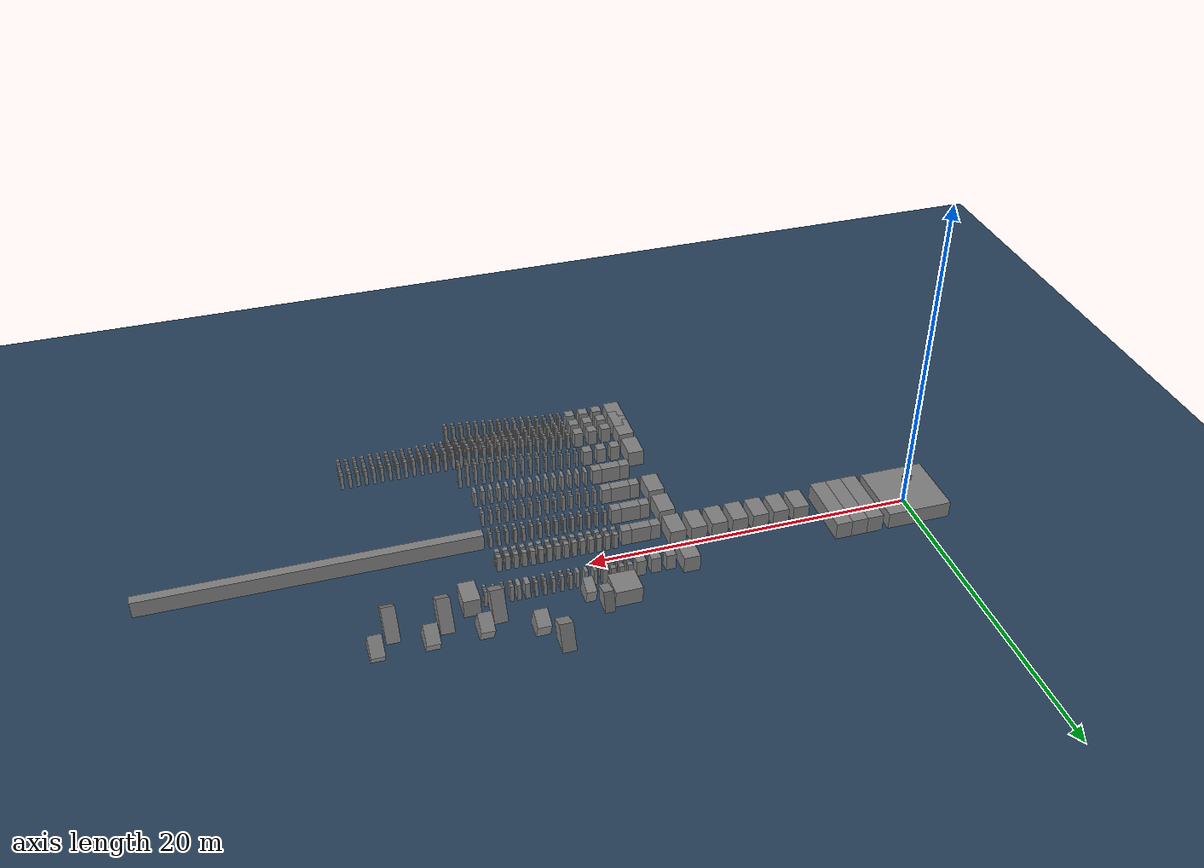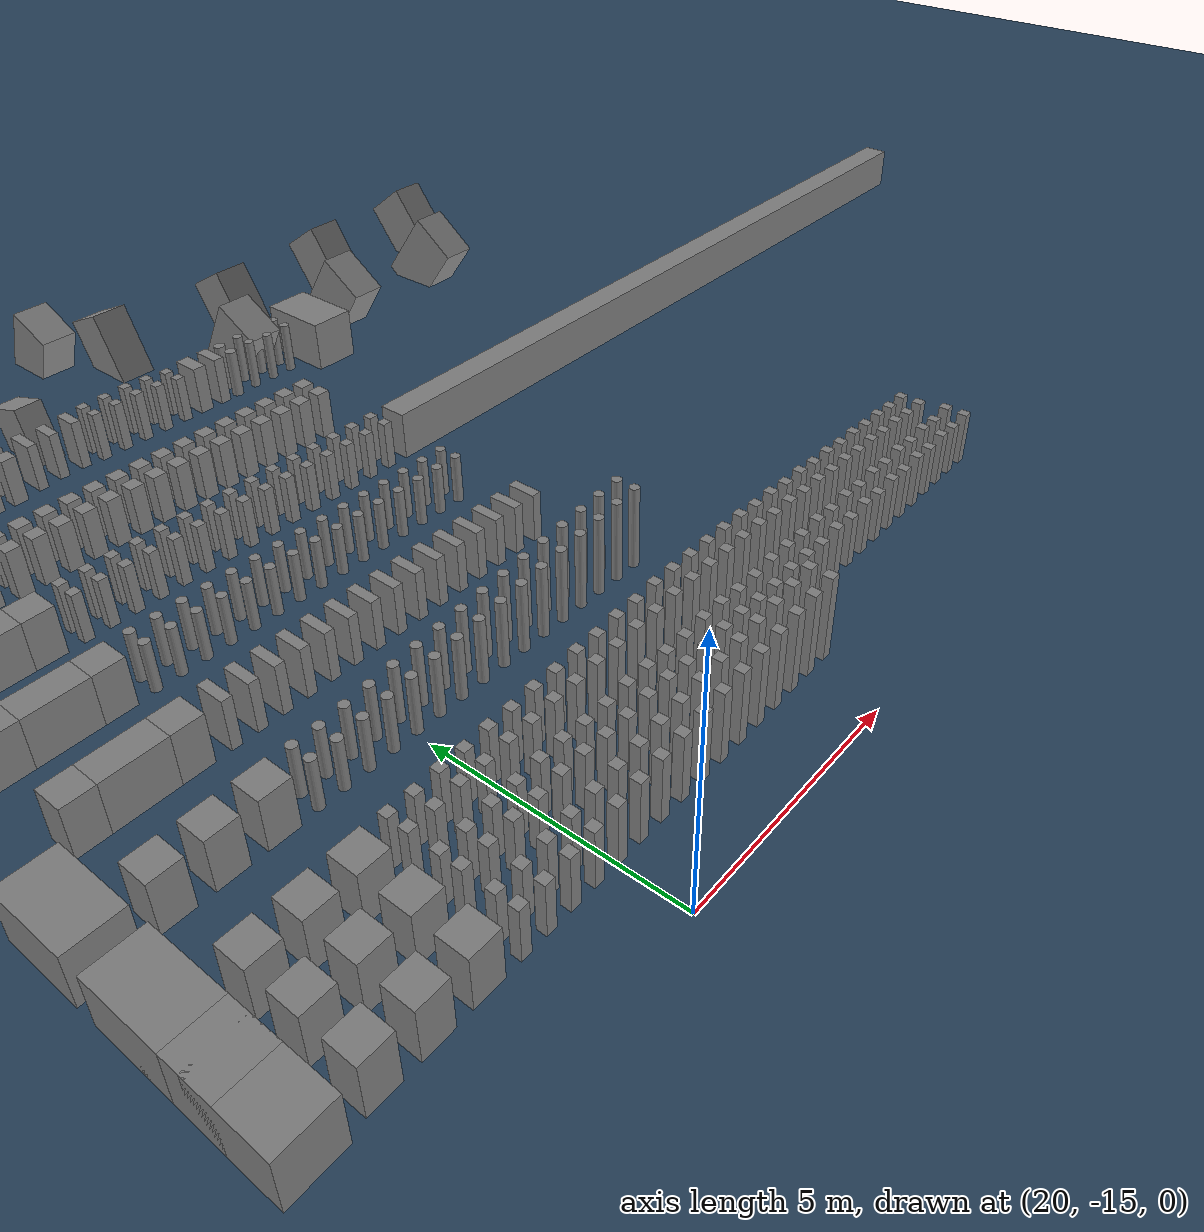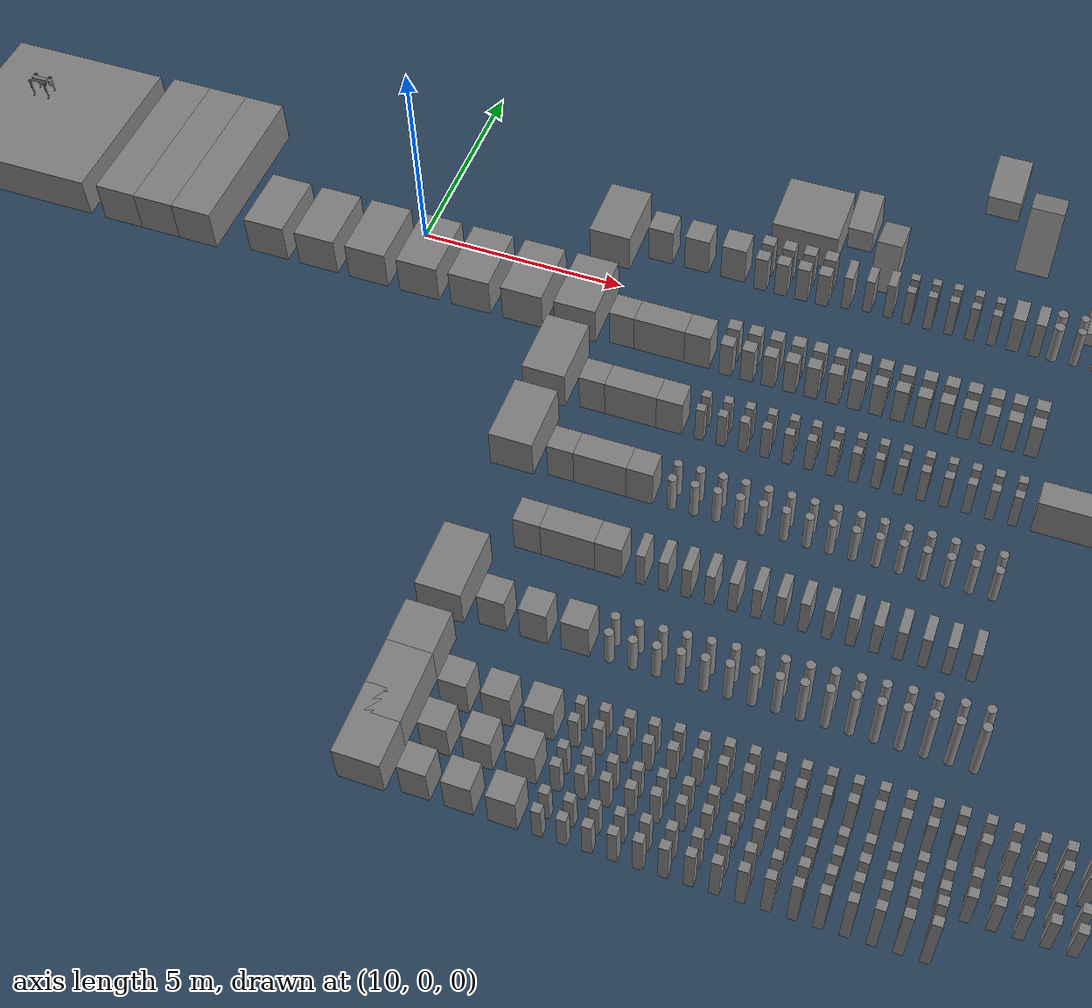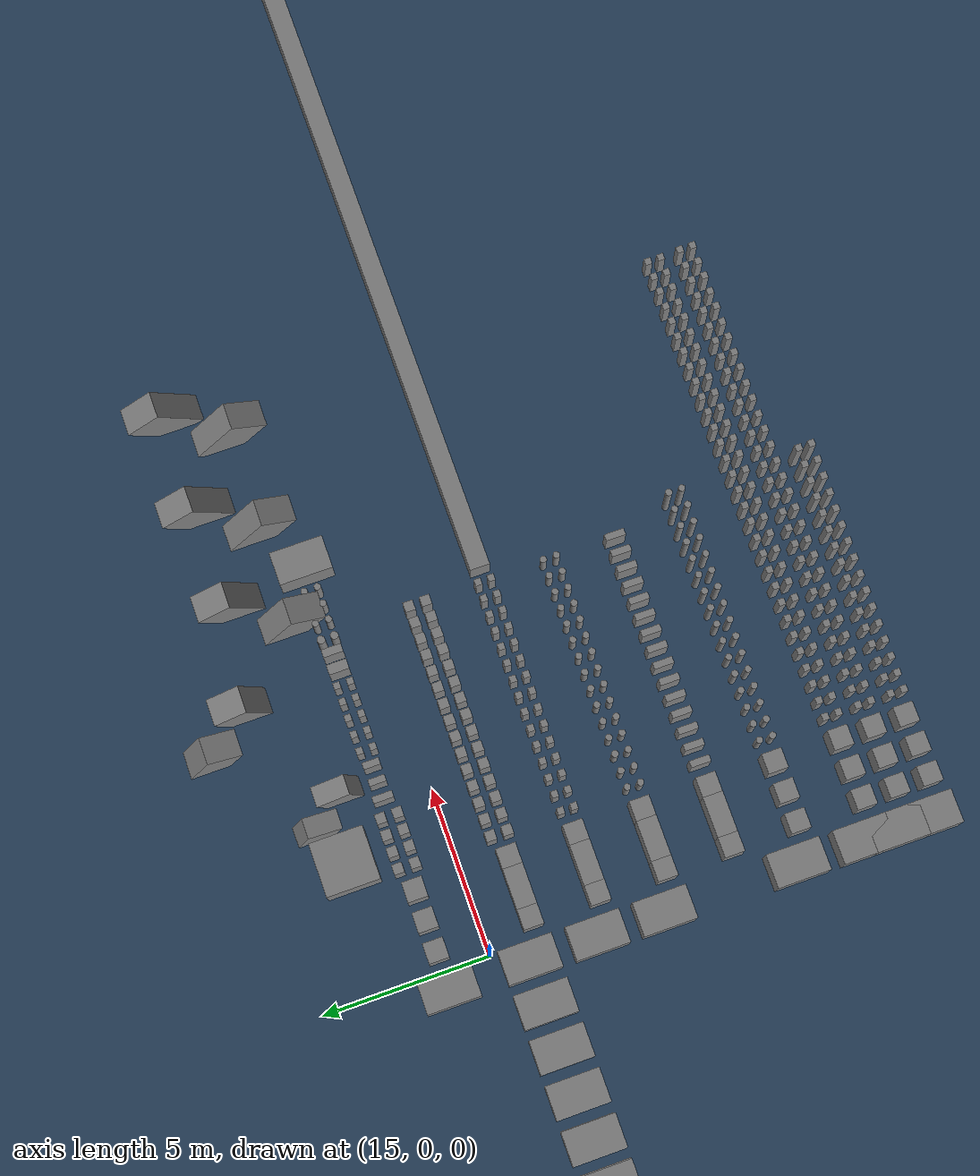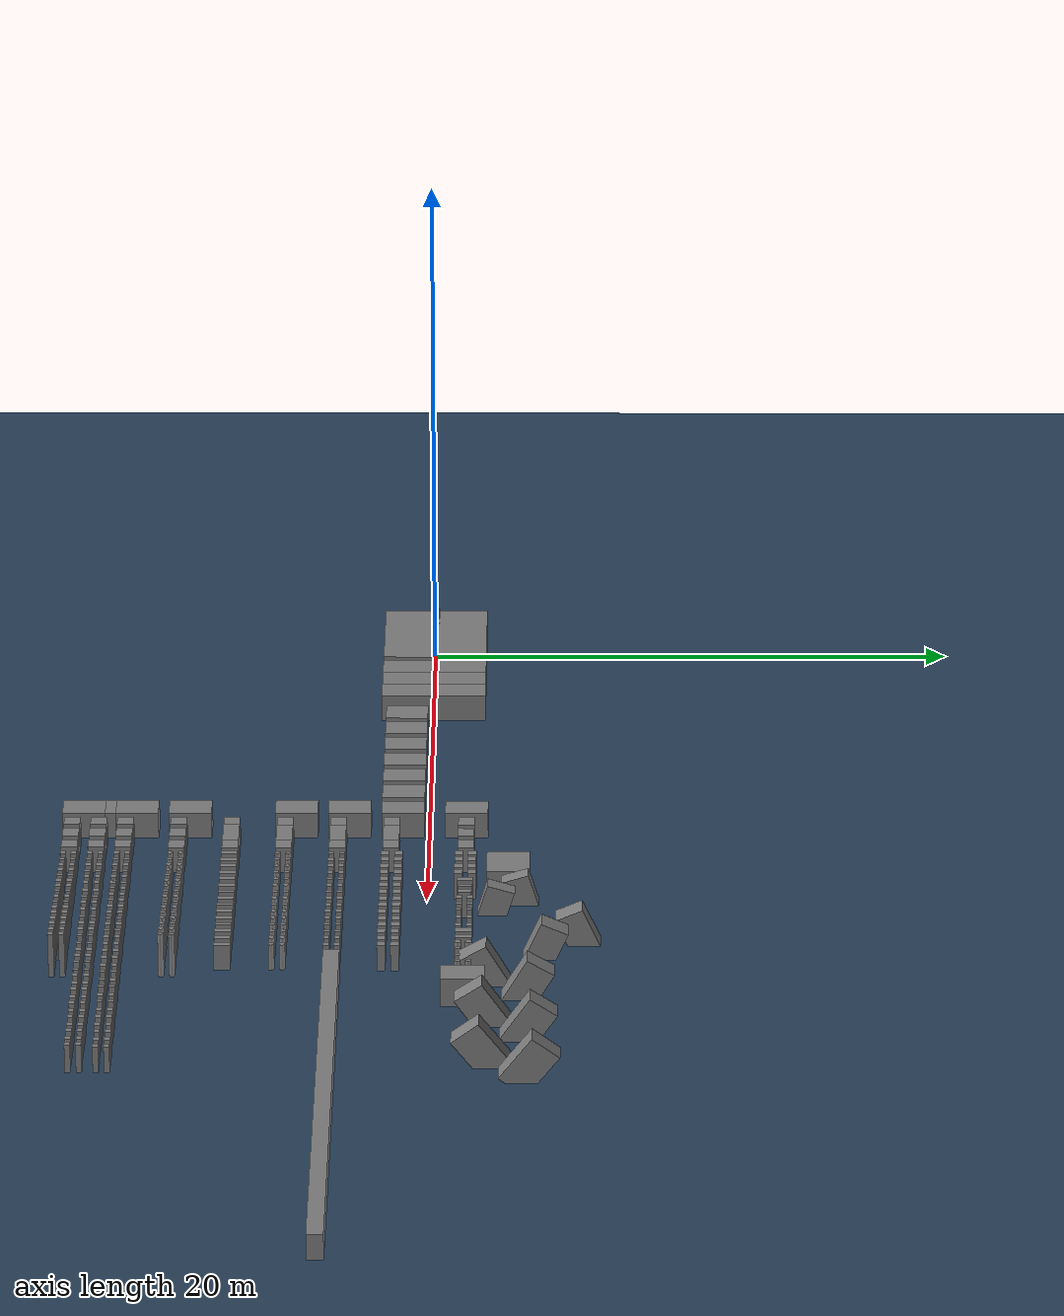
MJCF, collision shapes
<mujoco model="go2 scene">
  <include file="go2.xml" />

  <statistic center="17.2 -5.4 1.0" extent="0.8" />

  <visual>
    <headlight diffuse="0.6 0.6 0.6" ambient="0.3 0.3 0.3" specular="0 0 0" />
    <rgba haze="0.15 0.25 0.35 1" />
    <global azimuth="-130" elevation="-20" />
  </visual>

  <asset>
    <texture type="skybox" builtin="gradient" rgb1="0.3 0.5 0.7" rgb2="0 0 0" width="512" height="3072" />
    <texture type="2d" name="groundplane" builtin="checker" mark="edge" rgb1="0.2 0.3 0.4" rgb2="0.1 0.2 0.3" markrgb="0.8 0.8 0.8" width="300" height="300" />
    <material name="groundplane" texture="groundplane" texuniform="true" texrepeat="5 5" reflectance="0.2" />
  <hfield name="perlin_hfield" size="5.0 5.0 0.6 0.6" file="../height_field.png" />
  <hfield name="image_hfield" size="1.0 1.0 0.02 0.1" file="../unitree_hfield.png" />
  <texture name="T_simpleWoodTable" type="cube" height="1" width="1" file="./metal1.png" />
  <material name="M_simpleWoodTable" texture="T_simpleWoodTable" rgba="0.8 0.8 0.8 1" shininess="0.2" reflectance="0.3" texuniform="false" />
  <texture name="Blue" type="cube" height="1" width="1" file="./blue.png" />
  <material name="Blue" texture="Blue" rgba="0.8 0.8 0.8 1" shininess="0.2" reflectance="0.3" texuniform="false" />

  <texture name="Wall" type="cube" height="10" width="10" file="./wall.png" />
  <material name="Wall" texture="Wall" rgba="0.8 0.8 0.8 1" shininess="0.2" reflectance="0.3" texuniform="false" />
  </asset>

  <worldbody>
    <light pos="0 0 1.5" dir="0 0 -1" directional="true" />
    <geom name="floor" size="0 0 0.05" type="plane" material="groundplane" />

    <geom pos="0.0 0.0 0.0" type="box" size="2.0 2.0 1.0" quat="1.0 0.0 0.0 0.0" />
    <geom pos="2.9 0.0 0.05" type="box" size="0.5 2.0 1.0" quat="1.0 0.0 0.0 0.0" />
    <geom pos="3.9 0.0 0.05" type="box" size="0.5 2.0 1.0" quat="1.0 0.0 0.0 0.0" />
    <geom pos="4.9 0.0 0.05" type="box" size="0.5 2.0 1.0" quat="1.0 0.0 0.0 0.0" />
    <geom pos="6.7 -1.0 0.0" type="box" size="0.5 0.8 1.0" quat="1.0 0.0 0.0 0.0" />
    <geom pos="8.0 -1.0 0.0" type="box" size="0.5 0.8 1.0" quat="1.0 0.0 0.0 0.0" />
    <geom pos="9.3 -1.0 0.0" type="box" size="0.5 0.8 1.0" quat="1.0 0.0 0.0 0.0" />
    <geom pos="10.6 -1.0 0.0" type="box" size="0.5 0.8 1.0" quat="1.0 0.0 0.0 0.0" />
    <geom pos="11.9 -1.0 0.0" type="box" size="0.5 0.8 1.0" quat="1.0 0.0 0.0 0.0" />
    <geom pos="13.2 -1.0 0.0" type="box" size="0.5 0.8 1.0" quat="1.0 0.0 0.0 0.0" />
    <geom pos="14.5 -1.0 0.0" type="box" size="0.5 0.8 1.0" quat="1.0 0.0 0.0 0.0" />
    <geom pos="15.6 -1.4 0.0" type="box" size="0.3 0.3 1.0" quat="1.0 0.0 0.0 0.0" />
    <geom pos="16.5 -1.4 0.0" type="box" size="0.6 0.3 1.0" quat="1.0 0.0 0.0 0.0" />
    <geom pos="17.4 -1.4 0.0" type="box" size="0.3 0.3 1.0" quat="1.0 0.0 0.0 0.0" />
    <!-- 30/20 flat -->
    <geom pos="18.1 -1.1 0.0" type="box" size="0.15 0.15 1.0" quat="1.0 0.0 0.0 0.0" />
    <geom pos="18.1 -1.6 0.0" type="box" size="0.15 0.15 1.0" quat="1.0 0.0 0.0 0.0" />
    <geom pos="18.6 -1.1 0.0" type="box" size="0.15 0.15 1.0" quat="1.0 0.0 0.0 0.0" />
    <geom pos="18.6 -1.6 0.0" type="box" size="0.15 0.15 1.0" quat="1.0 0.0 0.0 0.0" />
    <geom pos="19.1 -1.1 0.0" type="box" size="0.15 0.15 1.0" quat="1.0 0.0 0.0 0.0" />
    <geom pos="19.1 -1.6 0.0" type="box" size="0.15 0.15 1.0" quat="1.0 0.0 0.0 0.0" />
    <geom pos="19.6 -1.1 0.0" type="box" size="0.15 0.15 1.0" quat="1.0 0.0 0.0 0.0" />
    <geom pos="19.6 -1.6 0.0" type="box" size="0.15 0.15 1.0" quat="1.0 0.0 0.0 0.0" />
    <geom pos="20.1 -1.1 0.0" type="box" size="0.15 0.15 1.0" quat="1.0 0.0 0.0 0.0" />
    <geom pos="20.1 -1.6 0.0" type="box" size="0.15 0.15 1.0" quat="1.0 0.0 0.0 0.0" />
    <geom pos="20.6 -1.1 0.0" type="box" size="0.15 0.15 1.0" quat="1.0 0.0 0.0 0.0" />
    <geom pos="20.6 -1.6 0.0" type="box" size="0.15 0.15 1.0" quat="1.0 0.0 0.0 0.0" />
    <geom pos="21.1 -1.1 0.0" type="box" size="0.15 0.15 1.0" quat="1.0 0.0 0.0 0.0" />
    <geom pos="21.1 -1.6 0.0" type="box" size="0.15 0.15 1.0" quat="1.0 0.0 0.0 0.0" />
    <geom pos="21.6 -1.1 0.0" type="box" size="0.15 0.15 1.0" quat="1.0 0.0 0.0 0.0" />
    <geom pos="21.6 -1.6 0.0" type="box" size="0.15 0.15 1.0" quat="1.0 0.0 0.0 0.0" />
    <geom pos="22.1 -1.1 0.0" type="box" size="0.15 0.15 1.0" quat="1.0 0.0 0.0 0.0" />
    <geom pos="22.1 -1.6 0.0" type="box" size="0.15 0.15 1.0" quat="1.0 0.0 0.0 0.0" />
    <geom pos="22.6 -1.1 0.0" type="box" size="0.15 0.15 1.0" quat="1.0 0.0 0.0 0.0" />
    <geom pos="22.6 -1.6 0.0" type="box" size="0.15 0.15 1.0" quat="1.0 0.0 0.0 0.0" />
    <geom pos="23.1 -1.1 0.0" type="box" size="0.15 0.15 1.0" quat="1.0 0.0 0.0 0.0" />
    <geom pos="23.1 -1.6 0.0" type="box" size="0.15 0.15 1.0" quat="1.0 0.0 0.0 0.0" />
    <geom pos="23.6 -1.1 0.0" type="box" size="0.15 0.15 1.0" quat="1.0 0.0 0.0 0.0" />
    <geom pos="23.6 -1.6 0.0" type="box" size="0.15 0.15 1.0" quat="1.0 0.0 0.0 0.0" />
    <geom pos="24.1 -1.1 0.0" type="box" size="0.15 0.15 1.0" quat="1.0 0.0 0.0 0.0" />
    <geom pos="24.1 -1.6 0.0" type="box" size="0.15 0.15 1.0" quat="1.0 0.0 0.0 0.0" />
    <geom pos="24.6 -1.1 0.0" type="box" size="0.15 0.15 1.0" quat="1.0 0.0 0.0 0.0" />
    <geom pos="24.6 -1.6 0.0" type="box" size="0.15 0.15 1.0" quat="1.0 0.0 0.0 0.0" />
    <geom pos="25.1 -1.1 0.0" type="box" size="0.15 0.15 1.0" quat="1.0 0.0 0.0 0.0" />
    <geom pos="25.1 -1.6 0.0" type="box" size="0.15 0.15 1.0" quat="1.0 0.0 0.0 0.0" />

    <!-- 20/30 flat -->
    <geom pos="14.5 -3.0 0.0" type="box" size="0.5 0.8 1.0" quat="1.0 0.0 0.0 0.0" />
    <geom pos="15.6 -3.4 0.0" type="box" size="0.3 0.3 1.0" quat="1.0 0.0 0.0 0.0" />
    <geom pos="16.5 -3.4 0.0" type="box" size="0.6 0.3 1.0" quat="1.0 0.0 0.0 0.0" />
    <geom pos="17.4 -3.4 0.0" type="box" size="0.3 0.3 1.0" quat="1.0 0.0 0.0 0.0" />
    <geom pos="18.1 -3.2 0.0" type="box" size="0.1 0.1 1.0" quat="1.0 0.0 0.0 0.0" />
    <geom pos="18.1 -3.6 0.0" type="box" size="0.1 0.1 1.0" quat="1.0 0.0 0.0 0.0" />
    <geom pos="18.6 -3.2 0.0" type="box" size="0.1 0.1 1.0" quat="1.0 0.0 0.0 0.0" />
    <geom pos="18.6 -3.6 0.0" type="box" size="0.1 0.1 1.0" quat="1.0 0.0 0.0 0.0" />
    <geom pos="19.1 -3.2 0.0" type="box" size="0.1 0.1 1.0" quat="1.0 0.0 0.0 0.0" />
    <geom pos="19.1 -3.6 0.0" type="box" size="0.1 0.1 1.0" quat="1.0 0.0 0.0 0.0" />
    <geom pos="19.6 -3.2 0.0" type="box" size="0.1 0.1 1.0" quat="1.0 0.0 0.0 0.0" />
    <geom pos="19.6 -3.6 0.0" type="box" size="0.1 0.1 1.0" quat="1.0 0.0 0.0 0.0" />
    <geom pos="20.1 -3.2 0.0" type="box" size="0.1 0.1 1.0" quat="1.0 0.0 0.0 0.0" />
    <geom pos="20.1 -3.6 0.0" type="box" size="0.1 0.1 1.0" quat="1.0 0.0 0.0 0.0" />
    <geom pos="20.6 -3.2 0.0" type="box" size="0.1 0.1 1.0" quat="1.0 0.0 0.0 0.0" />
    <geom pos="20.6 -3.6 0.0" type="box" size="0.1 0.1 1.0" quat="1.0 0.0 0.0 0.0" />
    <geom pos="21.1 -3.2 0.0" type="box" size="0.1 0.1 1.0" quat="1.0 0.0 0.0 0.0" />
    <geom pos="21.1 -3.6 0.0" type="box" size="0.1 0.1 1.0" quat="1.0 0.0 0.0 0.0" />
    <geom pos="21.6 -3.2 0.0" type="box" size="0.1 0.1 1.0" quat="1.0 0.0 0.0 0.0" />
    <geom pos="21.6 -3.6 0.0" type="box" size="0.1 0.1 1.0" quat="1.0 0.0 0.0 0.0" />
    <geom pos="22.1 -3.2 0.0" type="box" size="0.1 0.1 1.0" quat="1.0 0.0 0.0 0.0" />
    <geom pos="22.1 -3.6 0.0" type="box" size="0.1 0.1 1.0" quat="1.0 0.0 0.0 0.0" />
    <geom pos="22.6 -3.2 0.0" type="box" size="0.1 0.1 1.0" quat="1.0 0.0 0.0 0.0" />
    <geom pos="22.6 -3.6 0.0" type="box" size="0.1 0.1 1.0" quat="1.0 0.0 0.0 0.0" />
    <geom pos="23.1 -3.2 0.0" type="box" size="0.1 0.1 1.0" quat="1.0 0.0 0.0 0.0" />
    <geom pos="23.1 -3.6 0.0" type="box" size="0.1 0.1 1.0" quat="1.0 0.0 0.0 0.0" />
    <geom pos="23.6 -3.2 0.0" type="box" size="0.1 0.1 1.0" quat="1.0 0.0 0.0 0.0" />
    <geom pos="23.6 -3.6 0.0" type="box" size="0.1 0.1 1.0" quat="1.0 0.0 0.0 0.0" />
    <geom pos="24.1 -3.2 0.0" type="box" size="0.1 0.1 1.0" quat="1.0 0.0 0.0 0.0" />
    <geom pos="24.1 -3.6 0.0" type="box" size="0.1 0.1 1.0" quat="1.0 0.0 0.0 0.0" />
    <geom pos="24.6 -3.2 0.0" type="box" size="0.1 0.1 1.0" quat="1.0 0.0 0.0 0.0" />
    <geom pos="24.6 -3.6 0.0" type="box" size="0.1 0.1 1.0" quat="1.0 0.0 0.0 0.0" />
    <geom pos="25.1 -3.2 0.0" type="box" size="0.1 0.1 1.0" quat="1.0 0.0 0.0 0.0" />
    <geom pos="25.1 -3.6 0.0" type="box" size="0.1 0.1 1.0" quat="1.0 0.0 0.0 0.0" />
    <geom pos="35.5 -3.4 0.0" type="box" size="10 0.3 1.0" quat="1.0 0.0 0.0 0.0" />

    <!-- cylinder flat -->
    <geom pos="14.5 -5.0 0.0" type="box" size="0.5 0.8 1.0" quat="1.0 0.0 0.0 0.0" />
    <geom pos="15.6 -5.4 0.0" type="box" size="0.3 0.3 1.0" quat="1.0 0.0 0.0 0.0" />
    <geom pos="16.5 -5.4 0.0" type="box" size="0.6 0.3 1.0" quat="1.0 0.0 0.0 0.0" />
    <geom pos="17.4 -5.4 0.0" type="box" size="0.3 0.3 1.0" quat="1.0 0.0 0.0 0.0" />
    <geom pos="18.1 -5.2 0.0" type="cylinder" size="0.1 1.0 1.0" quat="1.0 0.0 0.0 0.0" />
    <geom pos="18.1 -5.6 0.0" type="cylinder" size="0.1 1.0 1.0" quat="1.0 0.0 0.0 0.0" />
    <geom pos="18.6 -5.2 0.0" type="cylinder" size="0.1 1.0 1.0" quat="1.0 0.0 0.0 0.0" />
    <geom pos="18.6 -5.6 0.0" type="cylinder" size="0.1 1.0 1.0" quat="1.0 0.0 0.0 0.0" />
    <geom pos="19.1 -5.2 0.0" type="cylinder" size="0.1 1.0 1.0" quat="1.0 0.0 0.0 0.0" />
    <geom pos="19.1 -5.6 0.0" type="cylinder" size="0.1 1.0 1.0" quat="1.0 0.0 0.0 0.0" />
    <geom pos="19.6 -5.2 0.0" type="cylinder" size="0.1 1.0 1.0" quat="1.0 0.0 0.0 0.0" />
    <geom pos="19.6 -5.6 0.0" type="cylinder" size="0.1 1.0 1.0" quat="1.0 0.0 0.0 0.0" />
    <geom pos="20.1 -5.2 0.0" type="cylinder" size="0.1 1.0 1.0" quat="1.0 0.0 0.0 0.0" />
    <geom pos="20.1 -5.6 0.0" type="cylinder" size="0.1 1.0 1.0" quat="1.0 0.0 0.0 0.0" />
    <geom pos="20.6 -5.2 0.0" type="cylinder" size="0.1 1.0 1.0" quat="1.0 0.0 0.0 0.0" />
    <geom pos="20.6 -5.6 0.0" type="cylinder" size="0.1 1.0 1.0" quat="1.0 0.0 0.0 0.0" />
    <geom pos="21.1 -5.2 0.0" type="cylinder" size="0.1 1.0 1.0" quat="1.0 0.0 0.0 0.0" />
    <geom pos="21.1 -5.6 0.0" type="cylinder" size="0.1 1.0 1.0" quat="1.0 0.0 0.0 0.0" />
    <geom pos="21.6 -5.2 0.0" type="cylinder" size="0.1 1.0 1.0" quat="1.0 0.0 0.0 0.0" />
    <geom pos="21.6 -5.6 0.0" type="cylinder" size="0.1 1.0 1.0" quat="1.0 0.0 0.0 0.0" />
    <geom pos="22.1 -5.2 0.0" type="cylinder" size="0.1 1.0 1.0" quat="1.0 0.0 0.0 0.0" />
    <geom pos="22.1 -5.6 0.0" type="cylinder" size="0.1 1.0 1.0" quat="1.0 0.0 0.0 0.0" />
    <geom pos="22.6 -5.2 0.0" type="cylinder" size="0.1 1.0 1.0" quat="1.0 0.0 0.0 0.0" />
    <geom pos="22.6 -5.6 0.0" type="cylinder" size="0.1 1.0 1.0" quat="1.0 0.0 0.0 0.0" />
    <geom pos="23.1 -5.2 0.0" type="cylinder" size="0.1 1.0 1.0" quat="1.0 0.0 0.0 0.0" />
    <geom pos="23.1 -5.6 0.0" type="cylinder" size="0.1 1.0 1.0" quat="1.0 0.0 0.0 0.0" />
    <geom pos="23.6 -5.2 0.0" type="cylinder" size="0.1 1.0 1.0" quat="1.0 0.0 0.0 0.0" />
    <geom pos="23.6 -5.6 0.0" type="cylinder" size="0.1 1.0 1.0" quat="1.0 0.0 0.0 0.0" />
    <geom pos="24.1 -5.2 0.0" type="cylinder" size="0.1 1.0 1.0" quat="1.0 0.0 0.0 0.0" />
    <geom pos="24.1 -5.6 0.0" type="cylinder" size="0.1 1.0 1.0" quat="1.0 0.0 0.0 0.0" />
    <geom pos="24.6 -5.2 0.0" type="cylinder" size="0.1 1.0 1.0" quat="1.0 0.0 0.0 0.0" />
    <geom pos="24.6 -5.6 0.0" type="cylinder" size="0.1 1.0 1.0" quat="1.0 0.0 0.0 0.0" />
    <geom pos="25.1 -5.2 0.0" type="cylinder" size="0.1 1.0 1.0" quat="1.0 0.0 0.0 0.0" />
    <geom pos="25.1 -5.6 0.0" type="cylinder" size="0.1 1.0 1.0" quat="1.0 0.0 0.0 0.0" />

    <geom pos="15.6 -7.4 0.0" type="box" size="0.3 0.3 1.0" quat="1.0 0.0 0.0 0.0" />
    <geom pos="16.5 -7.4 0.0" type="box" size="0.6 0.3 1.0" quat="1.0 0.0 0.0 0.0" />
    <geom pos="17.4 -7.4 0.0" type="box" size="0.3 0.3 1.0" quat="1.0 0.0 0.0 0.0" />
    <geom pos="18.1 -7.4 0.0" type="box" size="0.1 0.3 1.0" quat="1.0 0.0 0.0 0.0" />
    <geom pos="18.6 -7.4 0.0" type="box" size="0.1 0.3 1.0" quat="1.0 0.0 0.0 0.0" />
    <geom pos="19.1 -7.4 0.0" type="box" size="0.1 0.3 1.0" quat="1.0 0.0 0.0 0.0" />
    <geom pos="19.6 -7.4 0.0" type="box" size="0.1 0.3 1.0" quat="1.0 0.0 0.0 0.0" />
    <geom pos="20.1 -7.4 0.0" type="box" size="0.1 0.3 1.0" quat="1.0 0.0 0.0 0.0" />
    <geom pos="20.6 -7.4 0.0" type="box" size="0.1 0.3 1.0" quat="1.0 0.0 0.0 0.0" />
    <geom pos="21.1 -7.4 0.0" type="box" size="0.1 0.3 1.0" quat="1.0 0.0 0.0 0.0" />
    <geom pos="21.6 -7.4 0.0" type="box" size="0.1 0.3 1.0" quat="1.0 0.0 0.0 0.0" />
    <geom pos="22.1 -7.4 0.0" type="box" size="0.1 0.3 1.0" quat="1.0 0.0 0.0 0.0" />
    <geom pos="22.6 -7.4 0.0" type="box" size="0.1 0.3 1.0" quat="1.0 0.0 0.0 0.0" />
    <geom pos="23.1 -7.4 0.0" type="box" size="0.1 0.3 1.0" quat="1.0 0.0 0.0 0.0" />
    <geom pos="23.6 -7.4 0.0" type="box" size="0.1 0.3 1.0" quat="1.0 0.0 0.0 0.0" />
    <geom pos="24.1 -7.4 0.0" type="box" size="0.1 0.3 1.0" quat="1.0 0.0 0.0 0.0" />
    <geom pos="24.6 -7.4 0.0" type="box" size="0.1 0.3 1.0" quat="1.0 0.0 0.0 0.0" />
    <geom pos="25.1 -7.4 0.0" type="box" size="0.1 0.3 1.0" quat="1.0 0.0 0.0 0.0" />

    <geom pos="14.5 -9.0 0.0" type="box" size="0.5 0.8 1.0" quat="1.0 0.0 0.0 0.0" />
    <geom pos="15.6 -9.4 0.0" type="box" size="0.3 0.3 1.0" quat="1.0 0.0 0.0 0.0" />
    <geom pos="16.5 -9.4 0.0" type="box" size="0.3 0.3 1.0" quat="1.0 0.0 0.0 0.0" />
    <geom pos="17.4 -9.4 0.0" type="box" size="0.3 0.3 1.0" quat="1.0 0.0 0.0 0.0" />
    <geom pos="18.1 -9.2 0.0" type="cylinder" size="0.1 1.0 1.0" quat="1.0 0.0 0.0 0.0" />
    <geom pos="18.1 -9.6 0.0" type="cylinder" size="0.1 1.0 1.0" quat="1.0 0.0 0.0 0.0" />
    <geom pos="18.6 -9.2 0.0" type="cylinder" size="0.1 1.0 1.0" quat="1.0 0.0 0.0 0.0" />
    <geom pos="18.6 -9.6 0.0" type="cylinder" size="0.1 1.0 1.0" quat="1.0 0.0 0.0 0.0" />
    <geom pos="19.1 -9.2 0.05" type="cylinder" size="0.1 1.0 1.0" quat="1.0 0.0 0.0 0.0" />
    <geom pos="19.1 -9.6 0.05" type="cylinder" size="0.1 1.0 1.0" quat="1.0 0.0 0.0 0.0" />
    <geom pos="19.6 -9.2 0.1" type="cylinder" size="0.1 1.0 1.0" quat="1.0 0.0 0.0 0.0" />
    <geom pos="19.6 -9.6 0.1" type="cylinder" size="0.1 1.0 1.0" quat="1.0 0.0 0.0 0.0" />
    <geom pos="20.1 -9.2 0.15" type="cylinder" size="0.1 1.0 1.0" quat="1.0 0.0 0.0 0.0" />
    <geom pos="20.1 -9.6 0.15" type="cylinder" size="0.1 1.0 1.0" quat="1.0 0.0 0.0 0.0" />
    <geom pos="20.6 -9.2 0.2" type="cylinder" size="0.1 1.0 1.0" quat="1.0 0.0 0.0 0.0" />
    <geom pos="20.6 -9.6 0.2" type="cylinder" size="0.1 1.0 1.0" quat="1.0 0.0 0.0 0.0" />
    <geom pos="21.1 -9.2 0.25" type="cylinder" size="0.1 1.0 1.0" quat="1.0 0.0 0.0 0.0" />
    <geom pos="21.1 -9.6 0.25" type="cylinder" size="0.1 1.0 1.0" quat="1.0 0.0 0.0 0.0" />
    <geom pos="21.6 -9.2 0.3" type="cylinder" size="0.1 1.0 1.0" quat="1.0 0.0 0.0 0.0" />
    <geom pos="21.6 -9.6 0.3" type="cylinder" size="0.1 1.0 1.0" quat="1.0 0.0 0.0 0.0" />
    <geom pos="22.1 -9.2 0.35" type="cylinder" size="0.1 1.0 1.0" quat="1.0 0.0 0.0 0.0" />
    <geom pos="22.1 -9.6 0.35" type="cylinder" size="0.1 1.0 1.0" quat="1.0 0.0 0.0 0.0" />
    <geom pos="22.6 -9.2 0.4" type="cylinder" size="0.1 1.0 1.0" quat="1.0 0.0 0.0 0.0" />
    <geom pos="22.6 -9.6 0.4" type="cylinder" size="0.1 1.0 1.0" quat="1.0 0.0 0.0 0.0" />
    <geom pos="23.1 -9.2 0.45" type="cylinder" size="0.1 1.0 1.0" quat="1.0 0.0 0.0 0.0" />
    <geom pos="23.1 -9.6 0.45" type="cylinder" size="0.1 1.0 1.0" quat="1.0 0.0 0.0 0.0" />
    <geom pos="23.6 -9.2 0.5" type="cylinder" size="0.1 1.0 1.0" quat="1.0 0.0 0.0 0.0" />
    <geom pos="23.6 -9.6 0.5" type="cylinder" size="0.1 1.0 1.0" quat="1.0 0.0 0.0 0.0" />
    <geom pos="24.1 -9.2 0.55" type="cylinder" size="0.1 1.0 1.0" quat="1.0 0.0 0.0 0.0" />
    <geom pos="24.1 -9.6 0.55" type="cylinder" size="0.1 1.0 1.0" quat="1.0 0.0 0.0 0.0" />
    <geom pos="24.6 -9.2 0.6" type="cylinder" size="0.1 1.0 1.0" quat="1.0 0.0 0.0 0.0" />
    <geom pos="24.6 -9.6 0.6" type="cylinder" size="0.1 1.0 1.0" quat="1.0 0.0 0.0 0.0" />
    <geom pos="25.1 -9.2 0.65" type="cylinder" size="0.1 1.0 1.0" quat="1.0 0.0 0.0 0.0" />
    <geom pos="25.1 -9.6 0.65" type="cylinder" size="0.1 1.0 1.0" quat="1.0 0.0 0.0 0.0" />
    <geom pos="25.6 -9.2 0.7" type="cylinder" size="0.1 1.0 1.0" quat="1.0 0.0 0.0 0.0" />
    <geom pos="25.6 -9.6 0.7" type="cylinder" size="0.1 1.0 1.0" quat="1.0 0.0 0.0 0.0" />

    <!-- stairs-5cm -->
    <geom pos="14.5 -11.0 0.0" type="box" size="0.5 0.8 1.0" quat="1.0 0.0 0.0 0.0" />
    <geom pos="15.6 -11.4 0.0" type="box" size="0.3 0.3 1.0" quat="1.0 0.0 0.0 0.0" />
    <geom pos="16.5 -11.4 0.0" type="box" size="0.3 0.3 1.0" quat="1.0 0.0 0.0 0.0" />
    <geom pos="17.4 -11.4 0.0" type="box" size="0.3 0.3 1.0" quat="1.0 0.0 0.0 0.0" />
    <geom pos="18.1 -11.2 0.0" type="box" size="0.1 0.1 1.0" quat="1.0 0.0 0.0 0.0" />
    <geom pos="18.1 -11.6 0.0" type="box" size="0.1 0.1 1.0" quat="1.0 0.0 0.0 0.0" />
    <geom pos="18.6 -11.2 0.0" type="box" size="0.1 0.1 1.0" quat="1.0 0.0 0.0 0.0" />
    <geom pos="18.6 -11.6 0.0" type="box" size="0.1 0.1 1.0" quat="1.0 0.0 0.0 0.0" />
    <geom pos="19.1 -11.2 0.05" type="box" size="0.1 0.1 1.0" quat="1.0 0.0 0.0 0.0" />
    <geom pos="19.1 -11.6 0.05" type="box" size="0.1 0.1 1.0" quat="1.0 0.0 0.0 0.0" />
    <geom pos="19.6 -11.2 0.05" type="box" size="0.1 0.1 1.0" quat="1.0 0.0 0.0 0.0" />
    <geom pos="19.6 -11.6 0.05" type="box" size="0.1 0.1 1.0" quat="1.0 0.0 0.0 0.0" />
    <geom pos="20.1 -11.2 0.1" type="box" size="0.1 0.1 1.0" quat="1.0 0.0 0.0 0.0" />
    <geom pos="20.1 -11.6 0.1" type="box" size="0.1 0.1 1.0" quat="1.0 0.0 0.0 0.0" />
    <geom pos="20.6 -11.2 0.1" type="box" size="0.1 0.1 1.0" quat="1.0 0.0 0.0 0.0" />
    <geom pos="20.6 -11.6 0.1" type="box" size="0.1 0.1 1.0" quat="1.0 0.0 0.0 0.0" />
    <geom pos="21.1 -11.2 0.15" type="box" size="0.1 0.1 1.0" quat="1.0 0.0 0.0 0.0" />
    <geom pos="21.1 -11.6 0.15" type="box" size="0.1 0.1 1.0" quat="1.0 0.0 0.0 0.0" />
    <geom pos="21.6 -11.2 0.15" type="box" size="0.1 0.1 1.0" quat="1.0 0.0 0.0 0.0" />
    <geom pos="21.6 -11.6 0.15" type="box" size="0.1 0.1 1.0" quat="1.0 0.0 0.0 0.0" />
    <geom pos="22.1 -11.2 0.2" type="box" size="0.1 0.1 1.0" quat="1.0 0.0 0.0 0.0" />
    <geom pos="22.1 -11.6 0.2" type="box" size="0.1 0.1 1.0" quat="1.0 0.0 0.0 0.0" />
    <geom pos="22.6 -11.2 0.2" type="box" size="0.1 0.1 1.0" quat="1.0 0.0 0.0 0.0" />
    <geom pos="22.6 -11.6 0.2" type="box" size="0.1 0.1 1.0" quat="1.0 0.0 0.0 0.0" />
    <geom pos="23.1 -11.2 0.25" type="box" size="0.1 0.1 1.0" quat="1.0 0.0 0.0 0.0" />
    <geom pos="23.1 -11.6 0.25" type="box" size="0.1 0.1 1.0" quat="1.0 0.0 0.0 0.0" />
    <geom pos="23.6 -11.2 0.25" type="box" size="0.1 0.1 1.0" quat="1.0 0.0 0.0 0.0" />
    <geom pos="23.6 -11.6 0.25" type="box" size="0.1 0.1 1.0" quat="1.0 0.0 0.0 0.0" />
    <geom pos="24.1 -11.2 0.3" type="box" size="0.1 0.1 1.0" quat="1.0 0.0 0.0 0.0" />
    <geom pos="24.1 -11.6 0.3" type="box" size="0.1 0.1 1.0" quat="1.0 0.0 0.0 0.0" />
    <geom pos="24.6 -11.2 0.3" type="box" size="0.1 0.1 1.0" quat="1.0 0.0 0.0 0.0" />
    <geom pos="24.6 -11.6 0.3" type="box" size="0.1 0.1 1.0" quat="1.0 0.0 0.0 0.0" />
    <geom pos="25.1 -11.2 0.3" type="box" size="0.1 0.1 1.0" quat="1.0 0.0 0.0 0.0" />
    <geom pos="25.1 -11.6 0.3" type="box" size="0.1 0.1 1.0" quat="1.0 0.0 0.0 0.0" />
    <geom pos="25.6 -11.2 0.3" type="box" size="0.1 0.1 1.0" quat="1.0 0.0 0.0 0.0" />
    <geom pos="25.6 -11.6 0.3" type="box" size="0.1 0.1 1.0" quat="1.0 0.0 0.0 0.0" />
    <geom pos="26.1 -11.2 0.3" type="box" size="0.1 0.1 1.0" quat="1.0 0.0 0.0 0.0" />
    <geom pos="26.1 -11.6 0.3" type="box" size="0.1 0.1 1.0" quat="1.0 0.0 0.0 0.0" />
    <geom pos="26.6 -11.2 0.3" type="box" size="0.1 0.1 1.0" quat="1.0 0.0 0.0 0.0" />
    <geom pos="26.6 -11.6 0.3" type="box" size="0.1 0.1 1.0" quat="1.0 0.0 0.0 0.0" />
    <geom pos="27.1 -11.2 0.25" type="box" size="0.1 0.1 1.0" quat="1.0 0.0 0.0 0.0" />
    <geom pos="27.1 -11.6 0.25" type="box" size="0.1 0.1 1.0" quat="1.0 0.0 0.0 0.0" />
    <geom pos="27.6 -11.2 0.25" type="box" size="0.1 0.1 1.0" quat="1.0 0.0 0.0 0.0" />
    <geom pos="27.6 -11.6 0.25" type="box" size="0.1 0.1 1.0" quat="1.0 0.0 0.0 0.0" />
    <geom pos="28.1 -11.2 0.2" type="box" size="0.1 0.1 1.0" quat="1.0 0.0 0.0 0.0" />
    <geom pos="28.1 -11.6 0.2" type="box" size="0.1 0.1 1.0" quat="1.0 0.0 0.0 0.0" />
    <geom pos="28.6 -11.2 0.2" type="box" size="0.1 0.1 1.0" quat="1.0 0.0 0.0 0.0" />
    <geom pos="28.6 -11.6 0.2" type="box" size="0.1 0.1 1.0" quat="1.0 0.0 0.0 0.0" />
    <geom pos="29.1 -11.2 0.15" type="box" size="0.1 0.1 1.0" quat="1.0 0.0 0.0 0.0" />
    <geom pos="29.1 -11.6 0.15" type="box" size="0.1 0.1 1.0" quat="1.0 0.0 0.0 0.0" />
    <geom pos="29.6 -11.2 0.15" type="box" size="0.1 0.1 1.0" quat="1.0 0.0 0.0 0.0" />
    <geom pos="29.6 -11.6 0.15" type="box" size="0.1 0.1 1.0" quat="1.0 0.0 0.0 0.0" />
    <geom pos="30.1 -11.2 0.1" type="box" size="0.1 0.1 1.0" quat="1.0 0.0 0.0 0.0" />
    <geom pos="30.1 -11.6 0.1" type="box" size="0.1 0.1 1.0" quat="1.0 0.0 0.0 0.0" />
    <geom pos="30.6 -11.2 0.1" type="box" size="0.1 0.1 1.0" quat="1.0 0.0 0.0 0.0" />
    <geom pos="30.6 -11.6 0.1" type="box" size="0.1 0.1 1.0" quat="1.0 0.0 0.0 0.0" />
    <geom pos="31.1 -11.2 0.05" type="box" size="0.1 0.1 1.0" quat="1.0 0.0 0.0 0.0" />
    <geom pos="31.1 -11.6 0.05" type="box" size="0.1 0.1 1.0" quat="1.0 0.0 0.0 0.0" />
    <geom pos="31.6 -11.2 0.05" type="box" size="0.1 0.1 1.0" quat="1.0 0.0 0.0 0.0" />
    <geom pos="31.6 -11.6 0.05" type="box" size="0.1 0.1 1.0" quat="1.0 0.0 0.0 0.0" />
    <geom pos="32.1 -11.2 0.0" type="box" size="0.1 0.1 1.0" quat="1.0 0.0 0.0 0.0" />
    <geom pos="32.1 -11.6 0.0" type="box" size="0.1 0.1 1.0" quat="1.0 0.0 0.0 0.0" />
    <geom pos="32.6 -11.2 0.0" type="box" size="0.1 0.1 1.0" quat="1.0 0.0 0.0 0.0" />
    <geom pos="32.6 -11.6 0.0" type="box" size="0.1 0.1 1.0" quat="1.0 0.0 0.0 0.0" />

    <!-- stairs-5cm up down-->
    <geom pos="14.5 -12.0 0.0" type="box" size="0.5 0.8 1.0" quat="1.0 0.0 0.0 0.0" />
    <geom pos="15.6 -12.4 0.0" type="box" size="0.3 0.3 1.0" quat="1.0 0.0 0.0 0.0" />
    <geom pos="16.5 -12.4 0.0" type="box" size="0.3 0.3 1.0" quat="1.0 0.0 0.0 0.0" />
    <geom pos="17.4 -12.4 0.0" type="box" size="0.3 0.3 1.0" quat="1.0 0.0 0.0 0.0" />
    <geom pos="18.1 -12.2 0.0" type="box" size="0.1 0.1 1.0" quat="1.0 0.0 0.0 0.0" />
    <geom pos="18.1 -12.6 0.0" type="box" size="0.1 0.1 1.0" quat="1.0 0.0 0.0 0.0" />
    <geom pos="18.6 -12.2 0.0" type="box" size="0.1 0.1 1.0" quat="1.0 0.0 0.0 0.0" />
    <geom pos="18.6 -12.6 0.0" type="box" size="0.1 0.1 1.0" quat="1.0 0.0 0.0 0.0" />
    <geom pos="19.1 -12.2 0.05" type="box" size="0.1 0.1 1.0" quat="1.0 0.0 0.0 0.0" />
    <geom pos="19.1 -12.6 0.05" type="box" size="0.1 0.1 1.0" quat="1.0 0.0 0.0 0.0" />
    <geom pos="19.6 -12.2 0.05" type="box" size="0.1 0.1 1.0" quat="1.0 0.0 0.0 0.0" />
    <geom pos="19.6 -12.6 0.05" type="box" size="0.1 0.1 1.0" quat="1.0 0.0 0.0 0.0" />
    <geom pos="20.1 -12.2 0.1" type="box" size="0.1 0.1 1.0" quat="1.0 0.0 0.0 0.0" />
    <geom pos="20.1 -12.6 0.1" type="box" size="0.1 0.1 1.0" quat="1.0 0.0 0.0 0.0" />
    <geom pos="20.6 -12.2 0.1" type="box" size="0.1 0.1 1.0" quat="1.0 0.0 0.0 0.0" />
    <geom pos="20.6 -12.6 0.1" type="box" size="0.1 0.1 1.0" quat="1.0 0.0 0.0 0.0" />
    <geom pos="21.1 -12.2 0.05" type="box" size="0.1 0.1 1.0" quat="1.0 0.0 0.0 0.0" />
    <geom pos="21.1 -12.6 0.05" type="box" size="0.1 0.1 1.0" quat="1.0 0.0 0.0 0.0" />
    <geom pos="21.6 -12.2 0.05" type="box" size="0.1 0.1 1.0" quat="1.0 0.0 0.0 0.0" />
    <geom pos="21.6 -12.6 0.05" type="box" size="0.1 0.1 1.0" quat="1.0 0.0 0.0 0.0" />
    <geom pos="22.1 -12.2 0.1" type="box" size="0.1 0.1 1.0" quat="1.0 0.0 0.0 0.0" />
    <geom pos="22.1 -12.6 0.1" type="box" size="0.1 0.1 1.0" quat="1.0 0.0 0.0 0.0" />
    <geom pos="22.6 -12.2 0.1" type="box" size="0.1 0.1 1.0" quat="1.0 0.0 0.0 0.0" />
    <geom pos="22.6 -12.6 0.1" type="box" size="0.1 0.1 1.0" quat="1.0 0.0 0.0 0.0" />
    <geom pos="23.1 -12.2 0.05" type="box" size="0.1 0.1 1.0" quat="1.0 0.0 0.0 0.0" />
    <geom pos="23.1 -12.6 0.05" type="box" size="0.1 0.1 1.0" quat="1.0 0.0 0.0 0.0" />
    <geom pos="23.6 -12.2 0.05" type="box" size="0.1 0.1 1.0" quat="1.0 0.0 0.0 0.0" />
    <geom pos="23.6 -12.6 0.05" type="box" size="0.1 0.1 1.0" quat="1.0 0.0 0.0 0.0" />
    <geom pos="24.1 -12.2 0.1" type="box" size="0.1 0.1 1.0" quat="1.0 0.0 0.0 0.0" />
    <geom pos="24.1 -12.6 0.1" type="box" size="0.1 0.1 1.0" quat="1.0 0.0 0.0 0.0" />
    <geom pos="24.6 -12.2 0.1" type="box" size="0.1 0.1 1.0" quat="1.0 0.0 0.0 0.0" />
    <geom pos="24.6 -12.6 0.1" type="box" size="0.1 0.1 1.0" quat="1.0 0.0 0.0 0.0" />
    <geom pos="25.1 -12.2 0.05" type="box" size="0.1 0.1 1.0" quat="1.0 0.0 0.0 0.0" />
    <geom pos="25.1 -12.6 0.05" type="box" size="0.1 0.1 1.0" quat="1.0 0.0 0.0 0.0" />
    <geom pos="25.6 -12.2 0.05" type="box" size="0.1 0.1 1.0" quat="1.0 0.0 0.0 0.0" />
    <geom pos="25.6 -12.6 0.05" type="box" size="0.1 0.1 1.0" quat="1.0 0.0 0.0 0.0" />
    <geom pos="26.1 -12.2 0.1" type="box" size="0.1 0.1 1.0" quat="1.0 0.0 0.0 0.0" />
    <geom pos="26.1 -12.6 0.1" type="box" size="0.1 0.1 1.0" quat="1.0 0.0 0.0 0.0" />
    <geom pos="26.6 -12.2 0.1" type="box" size="0.1 0.1 1.0" quat="1.0 0.0 0.0 0.0" />
    <geom pos="26.6 -12.6 0.1" type="box" size="0.1 0.1 1.0" quat="1.0 0.0 0.0 0.0" />
    <geom pos="27.1 -12.2 0.05" type="box" size="0.1 0.1 1.0" quat="1.0 0.0 0.0 0.0" />
    <geom pos="27.1 -12.6 0.05" type="box" size="0.1 0.1 1.0" quat="1.0 0.0 0.0 0.0" />
    <geom pos="27.6 -12.2 0.1" type="box" size="0.1 0.1 1.0" quat="1.0 0.0 0.0 0.0" />
    <geom pos="27.6 -12.6 0.1" type="box" size="0.1 0.1 1.0" quat="1.0 0.0 0.0 0.0" />
    <geom pos="28.1 -12.2 0.05" type="box" size="0.1 0.1 1.0" quat="1.0 0.0 0.0 0.0" />
    <geom pos="28.1 -12.6 0.05" type="box" size="0.1 0.1 1.0" quat="1.0 0.0 0.0 0.0" />
    <geom pos="28.6 -12.2 0.1" type="box" size="0.1 0.1 1.0" quat="1.0 0.0 0.0 0.0" />
    <geom pos="28.6 -12.6 0.1" type="box" size="0.1 0.1 1.0" quat="1.0 0.0 0.0 0.0" />
    <geom pos="29.1 -12.2 0.05" type="box" size="0.1 0.1 1.0" quat="1.0 0.0 0.0 0.0" />
    <geom pos="29.1 -12.6 0.05" type="box" size="0.1 0.1 1.0" quat="1.0 0.0 0.0 0.0" />
    <geom pos="29.6 -12.2 0.1" type="box" size="0.1 0.1 1.0" quat="1.0 0.0 0.0 0.0" />
    <geom pos="29.6 -12.6 0.1" type="box" size="0.1 0.1 1.0" quat="1.0 0.0 0.0 0.0" />
    <geom pos="30.1 -12.2 0.05" type="box" size="0.1 0.1 1.0" quat="1.0 0.0 0.0 0.0" />
    <geom pos="30.1 -12.6 0.05" type="box" size="0.1 0.1 1.0" quat="1.0 0.0 0.0 0.0" />
    <geom pos="30.6 -12.2 0.1" type="box" size="0.1 0.1 1.0" quat="1.0 0.0 0.0 0.0" />
    <geom pos="30.6 -12.6 0.1" type="box" size="0.1 0.1 1.0" quat="1.0 0.0 0.0 0.0" />
    <geom pos="31.1 -12.2 0.05" type="box" size="0.1 0.1 1.0" quat="1.0 0.0 0.0 0.0" />
    <geom pos="31.1 -12.6 0.05" type="box" size="0.1 0.1 1.0" quat="1.0 0.0 0.0 0.0" />
    <geom pos="31.6 -12.2 0.1" type="box" size="0.1 0.1 1.0" quat="1.0 0.0 0.0 0.0" />
    <geom pos="31.6 -12.6 0.1" type="box" size="0.1 0.1 1.0" quat="1.0 0.0 0.0 0.0" />
    <geom pos="32.1 -12.2 0.05" type="box" size="0.1 0.1 1.0" quat="1.0 0.0 0.0 0.0" />
    <geom pos="32.1 -12.6 0.05" type="box" size="0.1 0.1 1.0" quat="1.0 0.0 0.0 0.0" />
    <geom pos="32.6 -12.2 0.1" type="box" size="0.1 0.1 1.0" quat="1.0 0.0 0.0 0.0" />
    <geom pos="32.6 -12.6 0.1" type="box" size="0.1 0.1 1.0" quat="1.0 0.0 0.0 0.0" />

    <!-- stairs-5cm continuous -->
    <geom pos="14.5 -13.0 0.0" type="box" size="0.5 0.8 1.0" quat="1.0 0.0 0.0 0.0" />
    <geom pos="15.6 -13.4 0.0" type="box" size="0.3 0.3 1.0" quat="1.0 0.0 0.0 0.0" />
    <geom pos="16.5 -13.4 0.0" type="box" size="0.3 0.3 1.0" quat="1.0 0.0 0.0 0.0" />
    <geom pos="17.4 -13.4 0.0" type="box" size="0.3 0.3 1.0" quat="1.0 0.0 0.0 0.0" />
    <geom pos="18.1 -13.2 0.0" type="box" size="0.1 0.1 1.0" quat="1.0 0.0 0.0 0.0" />
    <geom pos="18.1 -13.6 0.0" type="box" size="0.1 0.1 1.0" quat="1.0 0.0 0.0 0.0" />
    <geom pos="18.6 -13.2 0.0" type="box" size="0.1 0.1 1.0" quat="1.0 0.0 0.0 0.0" />
    <geom pos="18.6 -13.6 0.0" type="box" size="0.1 0.1 1.0" quat="1.0 0.0 0.0 0.0" />
    <geom pos="19.1 -13.2 0.05" type="box" size="0.1 0.1 1.0" quat="1.0 0.0 0.0 0.0" />
    <geom pos="19.1 -13.6 0.05" type="box" size="0.1 0.1 1.0" quat="1.0 0.0 0.0 0.0" />
    <geom pos="19.6 -13.2 0.1" type="box" size="0.1 0.1 1.0" quat="1.0 0.0 0.0 0.0" />
    <geom pos="19.6 -13.6 0.1" type="box" size="0.1 0.1 1.0" quat="1.0 0.0 0.0 0.0" />
    <geom pos="20.1 -13.2 0.15" type="box" size="0.1 0.1 1.0" quat="1.0 0.0 0.0 0.0" />
    <geom pos="20.1 -13.6 0.15" type="box" size="0.1 0.1 1.0" quat="1.0 0.0 0.0 0.0" />
    <geom pos="20.6 -13.2 0.2" type="box" size="0.1 0.1 1.0" quat="1.0 0.0 0.0 0.0" />
    <geom pos="20.6 -13.6 0.2" type="box" size="0.1 0.1 1.0" quat="1.0 0.0 0.0 0.0" />
    <geom pos="21.1 -13.2 0.25" type="box" size="0.1 0.1 1.0" quat="1.0 0.0 0.0 0.0" />
    <geom pos="21.1 -13.6 0.25" type="box" size="0.1 0.1 1.0" quat="1.0 0.0 0.0 0.0" />
    <geom pos="21.6 -13.2 0.3" type="box" size="0.1 0.1 1.0" quat="1.0 0.0 0.0 0.0" />
    <geom pos="21.6 -13.6 0.3" type="box" size="0.1 0.1 1.0" quat="1.0 0.0 0.0 0.0" />
    <geom pos="22.1 -13.2 0.35" type="box" size="0.1 0.1 1.0" quat="1.0 0.0 0.0 0.0" />
    <geom pos="22.1 -13.6 0.35" type="box" size="0.1 0.1 1.0" quat="1.0 0.0 0.0 0.0" />
    <geom pos="22.6 -13.2 0.4" type="box" size="0.1 0.1 1.0" quat="1.0 0.0 0.0 0.0" />
    <geom pos="22.6 -13.6 0.4" type="box" size="0.1 0.1 1.0" quat="1.0 0.0 0.0 0.0" />
    <geom pos="23.1 -13.2 0.45" type="box" size="0.1 0.1 1.0" quat="1.0 0.0 0.0 0.0" />
    <geom pos="23.1 -13.6 0.45" type="box" size="0.1 0.1 1.0" quat="1.0 0.0 0.0 0.0" />
    <geom pos="23.6 -13.2 0.5" type="box" size="0.1 0.1 1.0" quat="1.0 0.0 0.0 0.0" />
    <geom pos="23.6 -13.6 0.5" type="box" size="0.1 0.1 1.0" quat="1.0 0.0 0.0 0.0" />
    <geom pos="24.1 -13.2 0.55" type="box" size="0.1 0.1 1.0" quat="1.0 0.0 0.0 0.0" />
    <geom pos="24.1 -13.6 0.55" type="box" size="0.1 0.1 1.0" quat="1.0 0.0 0.0 0.0" />
    <geom pos="24.6 -13.2 0.6" type="box" size="0.1 0.1 1.0" quat="1.0 0.0 0.0 0.0" />
    <geom pos="24.6 -13.6 0.6" type="box" size="0.1 0.1 1.0" quat="1.0 0.0 0.0 0.0" />
    <geom pos="25.1 -13.2 0.65" type="box" size="0.1 0.1 1.0" quat="1.0 0.0 0.0 0.0" />
    <geom pos="25.1 -13.6 0.65" type="box" size="0.1 0.1 1.0" quat="1.0 0.0 0.0 0.0" />
    <geom pos="25.6 -13.2 0.7" type="box" size="0.1 0.1 1.0" quat="1.0 0.0 0.0 0.0" />
    <geom pos="25.6 -13.6 0.7" type="box" size="0.1 0.1 1.0" quat="1.0 0.0 0.0 0.0" />

    <!-- hybrid-->
    <geom pos="14.5 1.4 0.0" type="box" size="0.5 0.8 1.0" quat="1.0 0.0 0.0 0.0" />
    <geom pos="15.6 1.4 0.0" type="box" size="0.3 0.3 1.0" quat="1.0 0.0 0.0 0.0" />
    <geom pos="16.5 1.4 0.0" type="box" size="0.3 0.3 1.0" quat="1.0 0.0 0.0 0.0" />
    <geom pos="17.4 1.4 0.0" type="box" size="0.3 0.3 1.0" quat="1.0 0.0 0.0 0.0" />
    <geom pos="18.1 1.15 0.0" type="box" size="0.15 0.15 1.0" quat="1.0 0.0 0.0 0.0" />
    <geom pos="18.1 1.65 0.0" type="box" size="0.15 0.15 1.0" quat="1.0 0.0 0.0 0.0" />
    <geom pos="18.6 1.15 0.0" type="box" size="0.15 0.15 1.0" quat="1.0 0.0 0.0 0.0" />
    <geom pos="18.6 1.65 0.0" type="box" size="0.15 0.15 1.0" quat="1.0 0.0 0.0 0.0" />
    <geom pos="19.1 1.15 0.0" type="box" size="0.15 0.15 1.0" quat="1.0 0.0 0.0 0.0" />
    <geom pos="19.1 1.65 0.0" type="box" size="0.15 0.15 1.0" quat="1.0 0.0 0.0 0.0" />
    <geom pos="19.6 1.15 0.0" type="box" size="0.15 0.15 1.0" quat="1.0 0.0 0.0 0.0" />
    <geom pos="19.6 1.65 0.0" type="box" size="0.15 0.15 1.0" quat="1.0 0.0 0.0 0.0" />
    <geom pos="20.15 1.4 0.0" type="box" size="0.1 0.3 1.0" quat="1.0 0.0 0.0 0.0" />
    <geom pos="20.65 1.4 0.0" type="box" size="0.1 0.25 1.0" quat="1.0 0.0 0.0 0.0" />
    <geom pos="21.15 1.4 0.05" type="box" size="0.1 0.25 1.0" quat="1.0 0.0 0.0 0.0" />
    <geom pos="21.6 1.2 0.05" type="box" size="0.1 0.1 1.0" quat="1.0 0.0 0.0 0.0" />
    <geom pos="21.6 1.6 0.05" type="box" size="0.1 0.1 1.0" quat="1.0 0.0 0.0 0.0" />
    <geom pos="22.1 1.2 0.06" type="box" size="0.1 0.1 1.0" quat="1.0 0.0 0.0 0.0" />
    <geom pos="22.1 1.6 0.06" type="box" size="0.1 0.1 1.0" quat="1.0 0.0 0.0 0.0" />
    <geom pos="22.6 1.2 0.08" type="box" size="0.1 0.1 1.0" quat="1.0 0.0 0.0 0.0" />
    <geom pos="22.6 1.6 0.08" type="box" size="0.1 0.1 1.0" quat="1.0 0.0 0.0 0.0" />
    <geom pos="23.1 1.2 0.05" type="box" size="0.1 0.1 1.0" quat="1.0 0.0 0.0 0.0" />
    <geom pos="23.1 1.6 0.05" type="box" size="0.1 0.1 1.0" quat="1.0 0.0 0.0 0.0" />
    <geom pos="23.6 1.2 0.0" type="box" size="0.1 0.1 1.0" quat="1.0 0.0 0.0 0.0" />
    <geom pos="23.6 1.6 0.0" type="box" size="0.1 0.1 1.0" quat="1.0 0.0 0.0 0.0" />
    <geom pos="24.1 1.4 0.05" type="box" size="0.15 0.3 1.0" quat="1.0 0.0 0.0 0.0" />
    <geom pos="24.6 1.4 0.05" type="box" size="0.12 0.3 1.0" quat="1.0 0.0 0.0 0.0" />
    <geom pos="25.0 1.2 0.05" type="cylinder" size="0.12 1.0 1.0" quat="1.0 0.0 0.0 0.0" />
    <geom pos="25.0 1.6 0.05" type="cylinder" size="0.12 1.0 1.0" quat="1.0 0.0 0.0 0.0" />
    <geom pos="25.5 1.2 0.08" type="cylinder" size="0.1 1.0 1.0" quat="1.0 0.0 0.0 0.0" />
    <geom pos="25.5 1.6 0.08" type="cylinder" size="0.1 1.0 1.0" quat="1.0 0.0 0.0 0.0" />
    <geom pos="26.0 1.2 0.06" type="cylinder" size="0.1 1.0 1.0" quat="1.0 0.0 0.0 0.0" />
    <geom pos="26.0 1.6 0.06" type="cylinder" size="0.1 1.0 1.0" quat="1.0 0.0 0.0 0.0" />
    <geom pos="26.5 1.2 0.1" type="cylinder" size="0.1 1.0 1.0" quat="1.0 0.0 0.0 0.0" />
    <geom pos="26.5 1.6 0.1" type="cylinder" size="0.1 1.0 1.0" quat="1.0 0.0 0.0 0.0" />
    <geom pos="27.4 1.4 0.1" type="box" size="0.5 0.8 1.0" quat="1.0 0.0 0.0 0.0" />

    <!-- ===================== 17 deg ===================== -->
<!-- 高差 = 1.0 * tan(17°) = 0.306 m -->
<geom pos="18.8 3.0 0.0" type="box" size="0.8 0.8 1.0" quat="1.0 0.0 0.0 0.0" />

<geom name="tilt17_left"
      pos="20.000 3.542372 0.096561"
      type="box"
      size="0.300000 0.522846 1.000000"
      quat="0.98901586 0.14780941 0.0 0.0" />

<geom name="tilt17_right"
      pos="20.8 2.457628 0.096561"
      type="box"
      size="0.300000 0.522846 1.000000"
      quat="0.98901586 -0.14780941 0.0 0.0" />

<!-- ===================== 24 deg ===================== -->
<!-- 高差 = 1.0 * tan(24°) = 0.445 m -->
<geom name="tilt24_left"
      pos="23.000 5.656737 0.309069"
      type="box"
      size="0.400000 0.547318 1.000000"
      quat="0.97814760 0.20791169 0.0 0.0" />

<geom name="tilt24_right"
      pos="24.050 4.343263 0.309069"
      type="box"
      size="0.400000 0.547318 1.000000"
      quat="0.97814760 -0.20791169 0.0 0.0" />

<!-- ===================== 30 deg ===================== -->
<!-- 高差 = 1.0 * tan(30°) = 0.577 m -->
<geom name="tilt30_left"
      pos="26.000 2.250000 0.422650"
      type="box"
      size="0.400000 0.577350 1.000000"
      quat="0.96592583 0.25881905 0.0 0.0" />

<geom name="tilt30_right"
      pos="27.050 3.750000 0.422650"
      type="box"
      size="0.400000 0.577350 1.000000"
      quat="0.96592583 -0.25881905 0.0 0.0" />

<!-- ===================== 34 deg ===================== -->
<!-- 高差 = 1.0 * tan(34°) = 0.675 m -->
<geom name="tilt34_left"
      pos="29.000 2.190807 0.508217"
      type="box"
      size="0.400000 0.603109 1.000000"
      quat="0.95630476 0.29237170 0.0 0.0" />

<geom name="tilt34_right"
      pos="30.050 3.809193 0.508217"
      type="box"
      size="0.400000 0.603109 1.000000"
      quat="0.95630476 -0.29237170 0.0 0.0" />

<!-- ===================== 37 deg ===================== -->
<!-- 高差 = 1.0 * tan(37°) = 0.754 m -->
<geom name="tilt37_left"
      pos="32.000 2.148185 0.578142"
      type="box"
      size="0.400000 0.626068 1.000000"
      quat="0.94832366 0.31730466 0.0 0.0" />

<geom name="tilt37_right"
      pos="33.050 3.851815 0.578142"
      type="box"
      size="0.400000 0.626068 1.000000"
      quat="0.94832366 -0.31730466 0.0 0.0" />

  </worldbody>
</mujoco>

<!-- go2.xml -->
<mujoco model="go2">
  <compiler angle="radian" meshdir="assets" autolimits="true" />

  <option cone="elliptic" impratio="100" />

  <extension>
    <!-- 啟用 ray caster plugin -->
    <plugin plugin="mujoco.sensor.ray_caster"/>
  </extension>

  <default>
    <default class="go2">
      <geom friction="0.4" margin="0.001" condim="1"/>
      <joint axis="0 1 0" damping="0.1" armature="0.01" frictionloss="0.2"/>
      <motor ctrlrange="-23.7 23.7"/>
      <default class="abduction">
        <joint axis="1 0 0" range="-1.0472 1.0472"/>
      </default>
      <default class="hip">
        <default class="front_hip">
          <joint range="-1.5708 3.4907"/>
        </default>
        <default class="back_hip">
          <joint range="-0.5236 4.5379"/>
        </default>
      </default>
      <default class="knee">
        <joint range="-2.7227 -0.83776"/>
        <motor ctrlrange="-45.43 45.43"/>
      </default>
      <default class="visual">
        <geom type="mesh" contype="0" conaffinity="0" group="2"/>
      </default>
      <default class="collision">
        <geom group="3"/>
        <default class="foot">
          <geom size="0.022" pos="-0.002 0 -0.213" priority="1" condim="6"
            friction="0.8 0.02 0.01"/>
        </default>
      </default>
    </default>
  </default>

  <asset>
    <material name="metal" rgba=".9 .95 .95 1" />
    <material name="black" rgba="0 0 0 1" />
    <material name="white" rgba="1 1 1 1" />
    <material name="gray" rgba="0.671705 0.692426 0.774270 1" />

    <mesh file="base_0.obj" />
    <mesh file="base_1.obj" />
    <mesh file="base_2.obj" />
    <mesh file="base_3.obj" />
    <mesh file="base_4.obj" />
    <mesh file="hip_0.obj" />
    <mesh file="hip_1.obj" />
    <mesh file="thigh_0.obj" />
    <mesh file="thigh_1.obj" />
    <mesh file="thigh_mirror_0.obj" />
    <mesh file="thigh_mirror_1.obj" />
    <mesh file="calf_0.obj" />
    <mesh file="calf_1.obj" />
    <mesh file="calf_mirror_0.obj" />
    <mesh file="calf_mirror_1.obj" />
    <mesh file="foot.obj" />
  </asset>

  <worldbody>
    <body name="base_link" pos="0 0 2.0" childclass="go2">
      <inertial pos="0.021112 0 -0.005366" quat="-0.000543471 0.713435 -0.00173769 0.700719"
        mass="6.921"
        diaginertia="0.107027 0.0980771 0.0244531" />
      <freejoint />
      <geom mesh="base_0" material="black" class="visual" />
      <geom mesh="base_1" material="black" class="visual" />
      <geom mesh="base_2" material="black" class="visual" />
      <geom mesh="base_3" material="white" class="visual" />
      <geom mesh="base_4" material="gray" class="visual" />
      <geom size="0.1881 0.04675 0.057" type="box" class="collision" />
      <geom size="0.05 0.045" pos="0.285 0 0.01" type="cylinder" class="collision" />
      <geom size="0.047" pos="0.293 0 -0.06" class="collision" />
      <site name="imu" pos="-0.02557 0 0.04232" />
      <camera name="height_cam" pos="0 0 0" quat="1 0 0 0"/>
      <body name="FL_hip" pos="0.1934 0.0465 0">
        <inertial pos="-0.0054 0.00194 -0.000105" quat="0.497014 0.499245 0.505462 0.498237"
          mass="0.678"
          diaginertia="0.00088403 0.000596003 0.000479967" />
        <joint name="FL_hip_joint" class="abduction" />
        <geom mesh="hip_0" material="metal" class="visual" />
        <geom mesh="hip_1" material="gray" class="visual" />
        <geom size="0.046 0.02" pos="0 0.08 0" quat="1 1 0 0" type="cylinder" class="collision" />
        <body name="FL_thigh" pos="0 0.0955 0">
          <inertial pos="-0.00374 -0.0223 -0.0327" quat="0.829533 0.0847635 -0.0200632 0.551623"
            mass="1.152"
            diaginertia="0.00594973 0.00584149 0.000878787" />
          <joint name="FL_thigh_joint" class="front_hip" />
          <geom mesh="thigh_0" material="metal" class="visual" />
          <geom mesh="thigh_1" material="gray" class="visual" />
          <geom size="0.1065 0.01225 0.017" pos="0 0 -0.1065" quat="0.707107 0 0.707107 0"
            type="box" class="collision" />
          <body name="FL_calf" pos="0 0 -0.213">
            <inertial pos="0.00629595 -0.000622121 -0.141417"
              quat="0.710672 0.00154099 -0.00450087 0.703508"
              mass="0.241352" diaginertia="0.0014901 0.00146356 5.31397e-05" />
            <joint name="FL_calf_joint" class="knee" />
            <geom mesh="calf_0" material="gray" class="visual" />
            <geom mesh="calf_1" material="black" class="visual" />
            <geom size="0.012 0.06" pos="0.008 0 -0.06" quat="0.994493 0 -0.104807 0"
              type="cylinder" class="collision" />
            <geom size="0.011 0.0325" pos="0.02 0 -0.148" quat="0.999688 0 0.0249974 0"
              type="cylinder" class="collision" />
            <geom pos="0 0 -0.213" mesh="foot" class="visual" material="black" />
            <geom name="FL" class="foot" />
            <body name="FL_foot" pos="0 0 -0.213" />
          </body>
        </body>
      </body>
      <body name="FR_hip" pos="0.1934 -0.0465 0">
        <inertial pos="-0.0054 -0.00194 -0.000105" quat="0.498237 0.505462 0.499245 0.497014"
          mass="0.678"
          diaginertia="0.00088403 0.000596003 0.000479967" />
        <joint name="FR_hip_joint" class="abduction" />
        <geom mesh="hip_0" material="metal" class="visual" quat="4.63268e-05 1 0 0" />
        <geom mesh="hip_1" material="gray" class="visual" quat="4.63268e-05 1 0 0" />
        <geom size="0.046 0.02" pos="0 -0.08 0" quat="0.707107 0.707107 0 0" type="cylinder"
          class="collision" />
        <body name="FR_thigh" pos="0 -0.0955 0">
          <inertial pos="-0.00374 0.0223 -0.0327" quat="0.551623 -0.0200632 0.0847635 0.829533"
            mass="1.152"
            diaginertia="0.00594973 0.00584149 0.000878787" />
          <joint name="FR_thigh_joint" class="front_hip" />
          <geom mesh="thigh_mirror_0" material="metal" class="visual" />
          <geom mesh="thigh_mirror_1" material="gray" class="visual" />
          <geom size="0.1065 0.01225 0.017" pos="0 0 -0.1065" quat="0.707107 0 0.707107 0"
            type="box" class="collision" />
          <body name="FR_calf" pos="0 0 -0.213">
            <inertial pos="0.00629595 0.000622121 -0.141417"
              quat="0.703508 -0.00450087 0.00154099 0.710672"
              mass="0.241352" diaginertia="0.0014901 0.00146356 5.31397e-05" />
            <joint name="FR_calf_joint" class="knee" />
            <geom mesh="calf_mirror_0" material="gray" class="visual" />
            <geom mesh="calf_mirror_1" material="black" class="visual" />
            <geom size="0.013 0.06" pos="0.01 0 -0.06" quat="0.995004 0 -0.0998334 0"
              type="cylinder" class="collision" />
            <geom size="0.011 0.0325" pos="0.02 0 -0.148" quat="0.999688 0 0.0249974 0"
              type="cylinder" class="collision" />
            <geom pos="0 0 -0.213" mesh="foot" class="visual" material="black" />
            <geom name="FR" class="foot" />
            <body name="FR_foot" pos="0 0 -0.213" />
          </body>
        </body>
      </body>
      <body name="RL_hip" pos="-0.1934 0.0465 0">
        <inertial pos="0.0054 0.00194 -0.000105" quat="0.505462 0.498237 0.497014 0.499245"
          mass="0.678"
          diaginertia="0.00088403 0.000596003 0.000479967" />
        <joint name="RL_hip_joint" class="abduction" />
        <geom mesh="hip_0" material="metal" class="visual" quat="4.63268e-05 0 1 0" />
        <geom mesh="hip_1" material="gray" class="visual" quat="4.63268e-05 0 1 0" />
        <geom size="0.046 0.02" pos="0 0.08 0" quat="0.707107 0.707107 0 0" type="cylinder"
          class="collision" />
        <body name="RL_thigh" pos="0 0.0955 0">
          <inertial pos="-0.00374 -0.0223 -0.0327" quat="0.829533 0.0847635 -0.0200632 0.551623"
            mass="1.152"
            diaginertia="0.00594973 0.00584149 0.000878787" />
          <joint name="RL_thigh_joint" class="back_hip" />
          <geom mesh="thigh_0" material="metal" class="visual" />
          <geom mesh="thigh_1" material="gray" class="visual" />
          <geom size="0.1065 0.01225 0.017" pos="0 0 -0.1065" quat="0.707107 0 0.707107 0"
            type="box" class="collision" />
          <body name="RL_calf" pos="0 0 -0.213">
            <inertial pos="0.00629595 -0.000622121 -0.141417"
              quat="0.710672 0.00154099 -0.00450087 0.703508"
              mass="0.241352" diaginertia="0.0014901 0.00146356 5.31397e-05" />
            <joint name="RL_calf_joint" class="knee" />
            <geom mesh="calf_0" material="gray" class="visual" />
            <geom mesh="calf_1" material="black" class="visual" />
            <geom size="0.013 0.06" pos="0.01 0 -0.06" quat="0.995004 0 -0.0998334 0"
              type="cylinder" class="collision" />
            <geom size="0.011 0.0325" pos="0.02 0 -0.148" quat="0.999688 0 0.0249974 0"
              type="cylinder" class="collision" />
            <geom pos="0 0 -0.213" mesh="foot" class="visual" material="black" />
            <geom name="RL" class="foot" />
            <body name="RL_foot" pos="0 0 -0.213" />
          </body>
        </body>
      </body>
      <body name="RR_hip" pos="-0.1934 -0.0465 0">
        <inertial pos="0.0054 -0.00194 -0.000105" quat="0.499245 0.497014 0.498237 0.505462"
          mass="0.678"
          diaginertia="0.00088403 0.000596003 0.000479967" />
        <joint name="RR_hip_joint" class="abduction" />
        <geom mesh="hip_0" material="metal" class="visual"
          quat="2.14617e-09 4.63268e-05 4.63268e-05 -1" />
        <geom mesh="hip_1" material="gray" class="visual"
          quat="2.14617e-09 4.63268e-05 4.63268e-05 -1" />
        <geom size="0.046 0.02" pos="0 -0.08 0" quat="0.707107 0.707107 0 0" type="cylinder"
          class="collision" />
        <body name="RR_thigh" pos="0 -0.0955 0">
          <inertial pos="-0.00374 0.0223 -0.0327" quat="0.551623 -0.0200632 0.0847635 0.829533"
            mass="1.152"
            diaginertia="0.00594973 0.00584149 0.000878787" />
          <joint name="RR_thigh_joint" class="back_hip" />
          <geom mesh="thigh_mirror_0" material="metal" class="visual" />
          <geom mesh="thigh_mirror_1" material="gray" class="visual" />
          <geom size="0.1065 0.01225 0.017" pos="0 0 -0.1065" quat="0.707107 0 0.707107 0"
            type="box" class="collision" />
          <body name="RR_calf" pos="0 0 -0.213">
            <inertial pos="0.00629595 0.000622121 -0.141417"
              quat="0.703508 -0.00450087 0.00154099 0.710672"
              mass="0.241352" diaginertia="0.0014901 0.00146356 5.31397e-05" />
            <joint name="RR_calf_joint" class="knee" />
            <geom mesh="calf_mirror_0" material="gray" class="visual" />
            <geom mesh="calf_mirror_1" material="black" class="visual" />
            <geom size="0.013 0.06" pos="0.01 0 -0.06" quat="0.995004 0 -0.0998334 0"
              type="cylinder" class="collision" />
            <geom size="0.011 0.0325" pos="0.02 0 -0.148" quat="0.999688 0 0.0249974 0"
              type="cylinder" class="collision" />
            <geom pos="0 0 -0.213" mesh="foot" class="visual" material="black" />
            <geom name="RR" class="foot" />
            <body name="RR_foot" pos="0 0 -0.213" />
          </body>
        </body>
      </body>
    </body>
  </worldbody>

  <actuator>
    <motor class="abduction" name="FR_hip" joint="FR_hip_joint" />
    <motor class="hip" name="FR_thigh" joint="FR_thigh_joint" />
    <motor class="knee" name="FR_calf" joint="FR_calf_joint" />
    <motor class="abduction" name="FL_hip" joint="FL_hip_joint" />
    <motor class="hip" name="FL_thigh" joint="FL_thigh_joint" />
    <motor class="knee" name="FL_calf" joint="FL_calf_joint" />
    <motor class="abduction" name="RR_hip" joint="RR_hip_joint" />
    <motor class="hip" name="RR_thigh" joint="RR_thigh_joint" />
    <motor class="knee" name="RR_calf" joint="RR_calf_joint" />
    <motor class="abduction" name="RL_hip" joint="RL_hip_joint" />
    <motor class="hip" name="RL_thigh" joint="RL_thigh_joint" />
    <motor class="knee" name="RL_calf" joint="RL_calf_joint" />
  </actuator>

  <sensor>
    <jointpos name="FR_hip_pos" joint="FR_hip_joint" />
    <jointpos name="FR_thigh_pos" joint="FR_thigh_joint" />
    <jointpos name="FR_calf_pos" joint="FR_calf_joint" />
    <jointpos name="FL_hip_pos" joint="FL_hip_joint" />
    <jointpos name="FL_thigh_pos" joint="FL_thigh_joint" />
    <jointpos name="FL_calf_pos" joint="FL_calf_joint" />
    <jointpos name="RR_hip_pos" joint="RR_hip_joint" />
    <jointpos name="RR_thigh_pos" joint="RR_thigh_joint" />
    <jointpos name="RR_calf_pos" joint="RR_calf_joint" />
    <jointpos name="RL_hip_pos" joint="RL_hip_joint" />
    <jointpos name="RL_thigh_pos" joint="RL_thigh_joint" />
    <jointpos name="RL_calf_pos" joint="RL_calf_joint" />

    <jointvel name="FR_hip_vel" joint="FR_hip_joint" />
    <jointvel name="FR_thigh_vel" joint="FR_thigh_joint" />
    <jointvel name="FR_calf_vel" joint="FR_calf_joint" />
    <jointvel name="FL_hip_vel" joint="FL_hip_joint" />
    <jointvel name="FL_thigh_vel" joint="FL_thigh_joint" />
    <jointvel name="FL_calf_vel" joint="FL_calf_joint" />
    <jointvel name="RR_hip_vel" joint="RR_hip_joint" />
    <jointvel name="RR_thigh_vel" joint="RR_thigh_joint" />
    <jointvel name="RR_calf_vel" joint="RR_calf_joint" />
    <jointvel name="RL_hip_vel" joint="RL_hip_joint" />
    <jointvel name="RL_thigh_vel" joint="RL_thigh_joint" />
    <jointvel name="RL_calf_vel" joint="RL_calf_joint" />

    <jointactuatorfrc name="FR_hip_torque" joint="FR_hip_joint" noise="0.01" />
    <jointactuatorfrc name="FR_thigh_torque" joint="FR_thigh_joint" noise="0.01" />
    <jointactuatorfrc name="FR_calf_torque" joint="FR_calf_joint" noise="0.01" />
    <jointactuatorfrc name="FL_hip_torque" joint="FL_hip_joint" noise="0.01" />
    <jointactuatorfrc name="FL_thigh_torque" joint="FL_thigh_joint" noise="0.01" />
    <jointactuatorfrc name="FL_calf_torque" joint="FL_calf_joint" noise="0.01" />
    <jointactuatorfrc name="RR_hip_torque" joint="RR_hip_joint" noise="0.01" />
    <jointactuatorfrc name="RR_thigh_torque" joint="RR_thigh_joint" noise="0.01" />
    <jointactuatorfrc name="RR_calf_torque" joint="RR_calf_joint" noise="0.01" />
    <jointactuatorfrc name="RL_hip_torque" joint="RL_hip_joint" noise="0.01" />
    <jointactuatorfrc name="RL_thigh_torque" joint="RL_thigh_joint" noise="0.01" />
    <jointactuatorfrc name="RL_calf_torque" joint="RL_calf_joint" noise="0.01" />

    <framequat name="imu_quat" objtype="site" objname="imu" />
    <gyro name="imu_gyro" site="imu" />
    <accelerometer name="imu_acc" site="imu" />

    <framepos name="frame_pos" objtype="site" objname="imu" />
    <framelinvel name="frame_vel" objtype="site" objname="imu" />
    <!-- 這個就是之後 RL 會用到的「高度掃描器」 -->
    <plugin name="height_scanner"
            plugin="mujoco.sensor.ray_caster"
            objtype="camera" objname="height_cam">

      <config key="type" value="yaw" />
      <config key="resolution" value="0.1" />
      <config key="size" value="1.0 1.6" />
      <config key="dis_range" value="0.01 6" />

      <config key="compute_time_log" value="1" />

      <config key="draw_hip_point" value="1 0.02" /> -->

      <config key="sensor_data_types" value="data" />
      <config key="noise_type" value="uniform" />
      <config key="noise_cfg" value="0 0 1" />

    </plugin>
  </sensor>

  <keyframe>
    <key name="home" qpos="17.2 -5.4 1.3 1 0 0 0 0 0.9 -1.8 0 0.9 -1.8 0 0.9 -1.8 0 0.9 -1.8"
      ctrl="0 0.9 -1.8 0 0.9 -1.8 0 0.9 -1.8 0 0.9 -1.8" />
  </keyframe>
</mujoco>
